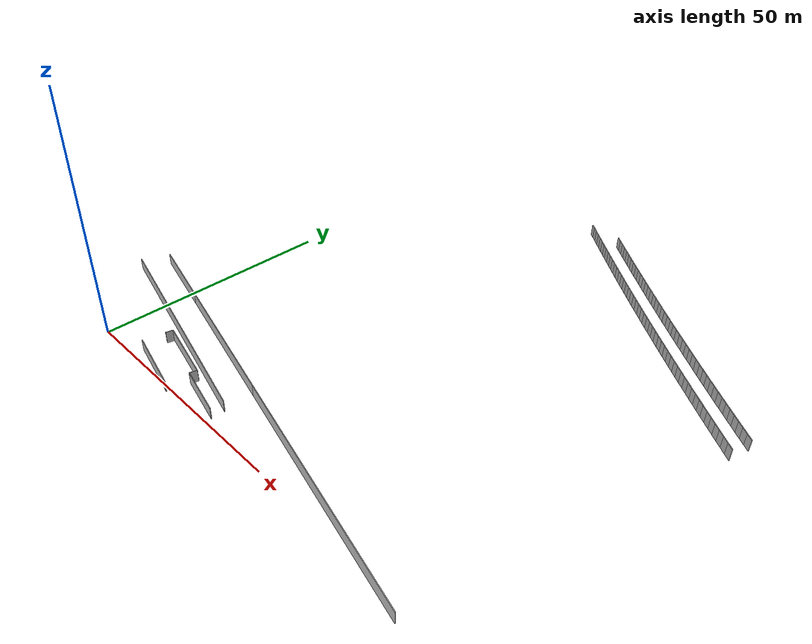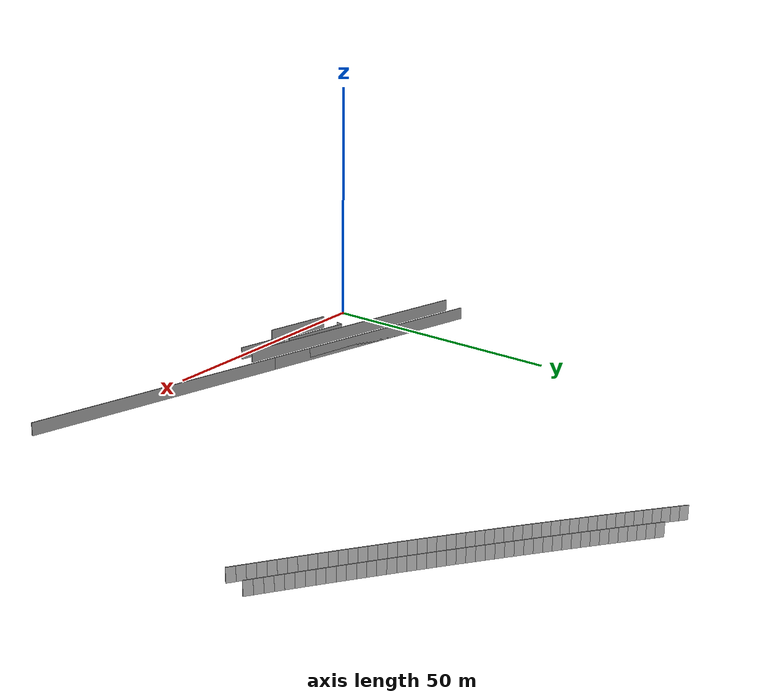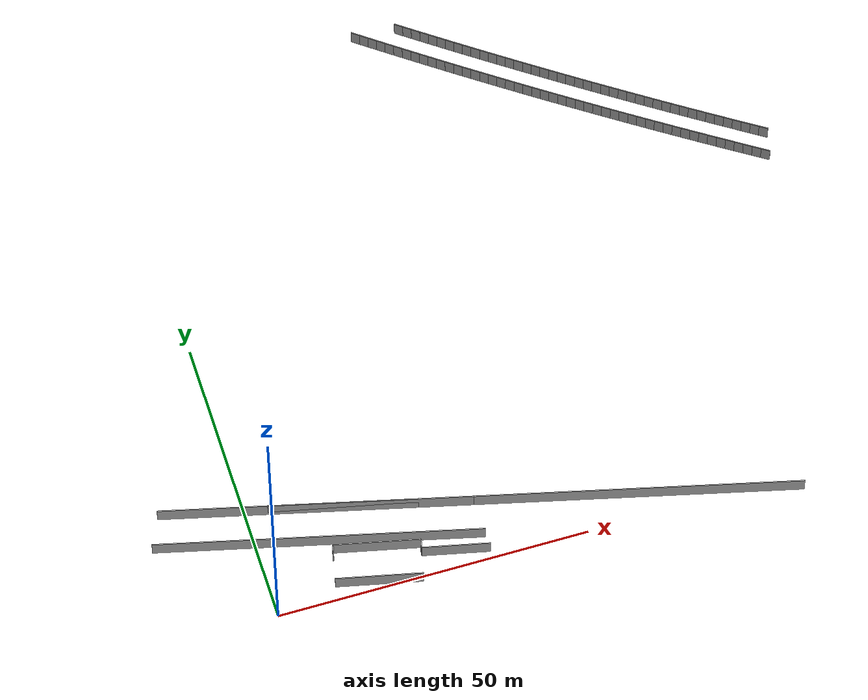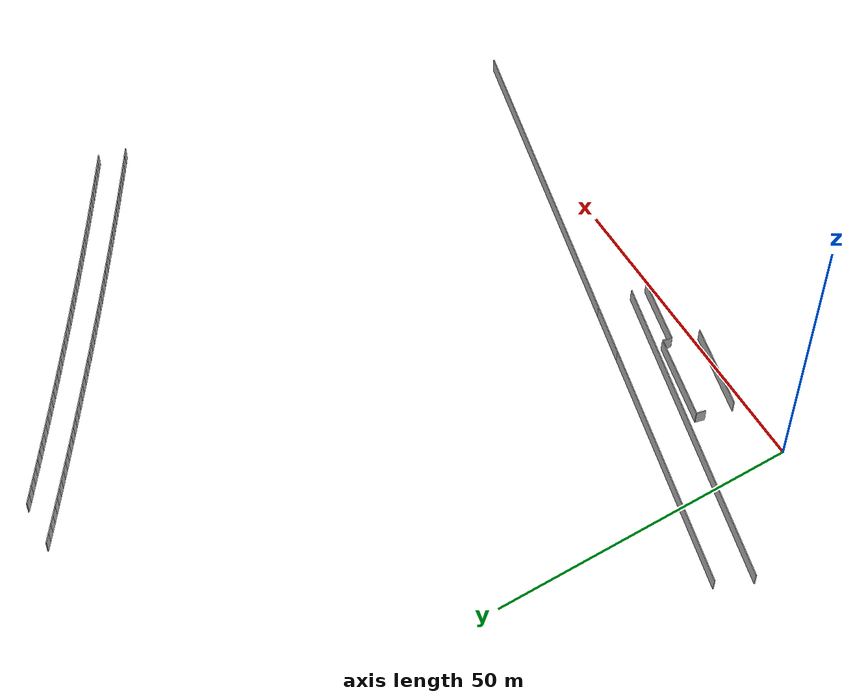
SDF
<?xml version="1.0" ?>
<sdf version="1.6">
  <model name="sps_0503">
    <pose frame="">0 0 0 0 -0 0</pose>
    <static>1</static>
    <self_collide>0</self_collide>
    <allow_auto_disable>0</allow_auto_disable>
    <link name="Wall104">
      <kinematic>0</kinematic>
      <gravity>1</gravity>
      <self_collide>0</self_collide>
      <collision name="collision">
        <geometry>
          <box>
            <size>51.5639 0.15 2.5</size>
          </box>
        </geometry>
        <pose frame="">0 0 0 0 -0 0</pose>
      </collision>
      <visual name="visual">
        <geometry>
          <box>
            <size>51.5639 0.15 2.5</size>
          </box>
        </geometry>
        <pose frame="">0 0 0 0 -0 0</pose>
        <cast_shadows>1</cast_shadows>
        <transparency>0.0</transparency>
      </visual>
      <pose frame="">9.46944 10.2681 1.25 0 0 -0.246916</pose>
    </link>
    <link name="Wall180">
      <kinematic>0</kinematic>
      <gravity>1</gravity>
      <self_collide>0</self_collide>
      <collision name="collision">
        <geometry>
          <box>
            <size>51.5805 0.15 2.5</size>
          </box>
        </geometry>
        <pose frame="">0 0 0 0 -0 0</pose>
      </collision>
      <visual name="visual">
        <geometry>
          <box>
            <size>51.5805 0.15 2.5</size>
          </box>
        </geometry>
        <pose frame="">0 0 0 0 -0 0</pose>
        <cast_shadows>1</cast_shadows>
        <transparency>0.0</transparency>
      </visual>
      <pose frame="">59.4694 3.69687 1.25 0 -0 2.89341</pose>
    </link>
    <link name="Wall181">
      <kinematic>0</kinematic>
      <gravity>1</gravity>
      <self_collide>0</self_collide>
      <collision name="collision">
        <geometry>
          <box>
            <size>32.001 0.15 2.5</size>
          </box>
        </geometry>
        <pose frame="">0 0 0 0 -0 0</pose>
      </collision>
      <visual name="visual">
        <geometry>
          <box>
            <size>32.001 0.15 2.5</size>
          </box>
        </geometry>
        <pose frame="">0 0 0 0 -0 0</pose>
        <cast_shadows>1</cast_shadows>
        <transparency>0.0</transparency>
      </visual>
      <pose frame="">18.9592 13.9626 1.25 0 -0 2.89341</pose>
    </link>
    <link name="Wall275">
      <kinematic>0</kinematic>
      <gravity>1</gravity>
      <self_collide>0</self_collide>
      <collision name="collision">
        <geometry>
          <box>
            <size>1.49953 0.15 2.5</size>
          </box>
        </geometry>
        <pose frame="">0 0 0 0 -0 0</pose>
      </collision>
      <visual name="visual">
        <geometry>
          <box>
            <size>1.49953 0.15 2.5</size>
          </box>
        </geometry>
        <pose frame="">0 0 0 0 -0 0</pose>
        <cast_shadows>1</cast_shadows>
        <transparency>0.0</transparency>
      </visual>
      <pose frame="">24.2309 4.40401 1.25 0 -0 1.34234</pose>
    </link>
    <link name="Wall337">
      <kinematic>0</kinematic>
      <gravity>1</gravity>
      <self_collide>0</self_collide>
      <collision name="collision">
        <geometry>
          <box>
            <size>13.6502 0.15 2.5</size>
          </box>
        </geometry>
        <pose frame="">0 0 0 0 -0 0</pose>
      </collision>
      <visual name="visual">
        <geometry>
          <box>
            <size>13.6502 0.15 2.5</size>
          </box>
        </geometry>
        <pose frame="">0 0 0 0 -0 0</pose>
        <cast_shadows>1</cast_shadows>
        <transparency>0.0</transparency>
      </visual>
      <pose frame="">16.3896 0.810378 1.25 0 -0 2.91335</pose>
    </link>
    <link name="Wall342">
      <kinematic>0</kinematic>
      <gravity>1</gravity>
      <self_collide>0</self_collide>
      <collision name="collision">
        <geometry>
          <box>
            <size>10.6855 0.15 2.5</size>
          </box>
        </geometry>
        <pose frame="">0 0 0 0 -0 0</pose>
      </collision>
      <visual name="visual">
        <geometry>
          <box>
            <size>10.6855 0.15 2.5</size>
          </box>
        </geometry>
        <pose frame="">0 0 0 0 -0 0</pose>
        <cast_shadows>1</cast_shadows>
        <transparency>0.0</transparency>
      </visual>
      <pose frame="">29.2653 2.46477 1.25 0 -0 2.91334</pose>
    </link>
    <link name="Wall421">
      <kinematic>0</kinematic>
      <gravity>1</gravity>
      <self_collide>0</self_collide>
      <collision name="collision">
        <geometry>
          <box>
            <size>13.6503 0.15 2.5</size>
          </box>
        </geometry>
        <pose frame="">0 0 0 0 -0 0</pose>
      </collision>
      <visual name="visual">
        <geometry>
          <box>
            <size>13.6503 0.15 2.5</size>
          </box>
        </geometry>
        <pose frame="">0 0 0 0 -0 0</pose>
        <cast_shadows>1</cast_shadows>
        <transparency>0.0</transparency>
      </visual>
      <pose frame="">17.7526 6.67909 1.25 0 -0 2.91327</pose>
    </link>
    <link name="Wall596">
      <kinematic>0</kinematic>
      <gravity>1</gravity>
      <self_collide>0</self_collide>
      <collision name="collision">
        <geometry>
          <box>
            <size>1.5008 0.15 2.5</size>
          </box>
        </geometry>
        <pose frame="">0 0 0 0 -0 0</pose>
      </collision>
      <visual name="visual">
        <geometry>
          <box>
            <size>1.5008 0.15 2.5</size>
          </box>
        </geometry>
        <pose frame="">0 0 0 0 -0 0</pose>
        <cast_shadows>1</cast_shadows>
        <transparency>0.0</transparency>
      </visual>
      <pose frame="">10.9351 7.4929 1.25 0 0 -1.79876</pose>
    </link>
    <link name="Wall1406">
      <kinematic>0</kinematic>
      <gravity>1</gravity>
      <self_collide>0</self_collide>
      <collision name="collision">
        <geometry>
          <box>
            <size>40.6119 0.15 2.5</size>
          </box>
        </geometry>
        <pose frame="">0 0 0 0 -0 0</pose>
      </collision>
      <visual name="visual">
        <geometry>
          <box>
            <size>40.6119 0.15 2.5</size>
          </box>
        </geometry>
        <pose frame="">0 0 0 0 -0 0</pose>
        <cast_shadows>1</cast_shadows>
        <transparency>0.0</transparency>
      </visual>
      <pose frame="">6.51485 17.1161 1.25 0 0 -0.248183</pose>
    </link>
    <link name="Wall8624">
      <kinematic>0</kinematic>
      <gravity>1</gravity>
      <self_collide>0</self_collide>
      <collision name="collision">
        <geometry>
          <box>
            <size>1.4989 0.15 2.5</size>
          </box>
        </geometry>
        <pose frame="">0 0 0 0 -0 0</pose>
      </collision>
      <visual name="visual">
        <geometry>
          <box>
            <size>1.4989 0.15 2.5</size>
          </box>
        </geometry>
        <pose frame="">0 0 0 0 -0 0</pose>
        <cast_shadows>1</cast_shadows>
        <transparency>0.0</transparency>
      </visual>
      <pose frame="">42.1988 99.8224 1.25 0 0 -0.672229</pose>
    </link>
    <link name="Wall8625">
      <kinematic>0</kinematic>
      <gravity>1</gravity>
      <self_collide>0</self_collide>
      <collision name="collision">
        <geometry>
          <box>
            <size>1.49893 0.15 2.5</size>
          </box>
        </geometry>
        <pose frame="">0 0 0 0 -0 0</pose>
      </collision>
      <visual name="visual">
        <geometry>
          <box>
            <size>1.49893 0.15 2.5</size>
          </box>
        </geometry>
        <pose frame="">0 0 0 0 -0 0</pose>
        <cast_shadows>1</cast_shadows>
        <transparency>0.0</transparency>
      </visual>
      <pose frame="">43.3725 98.89 1.25 0 0 -0.670493</pose>
    </link>
    <link name="Wall8626">
      <kinematic>0</kinematic>
      <gravity>1</gravity>
      <self_collide>0</self_collide>
      <collision name="collision">
        <geometry>
          <box>
            <size>1.49896 0.15 2.5</size>
          </box>
        </geometry>
        <pose frame="">0 0 0 0 -0 0</pose>
      </collision>
      <visual name="visual">
        <geometry>
          <box>
            <size>1.49896 0.15 2.5</size>
          </box>
        </geometry>
        <pose frame="">0 0 0 0 -0 0</pose>
        <cast_shadows>1</cast_shadows>
        <transparency>0.0</transparency>
      </visual>
      <pose frame="">44.5476 97.9594 1.25 0 0 -0.669075</pose>
    </link>
    <link name="Wall8627">
      <kinematic>0</kinematic>
      <gravity>1</gravity>
      <self_collide>0</self_collide>
      <collision name="collision">
        <geometry>
          <box>
            <size>1.49874 0.15 2.5</size>
          </box>
        </geometry>
        <pose frame="">0 0 0 0 -0 0</pose>
      </collision>
      <visual name="visual">
        <geometry>
          <box>
            <size>1.49874 0.15 2.5</size>
          </box>
        </geometry>
        <pose frame="">0 0 0 0 -0 0</pose>
        <cast_shadows>1</cast_shadows>
        <transparency>0.0</transparency>
      </visual>
      <pose frame="">45.7241 97.0307 1.25 0 0 -0.667376</pose>
    </link>
    <link name="Wall8628">
      <kinematic>0</kinematic>
      <gravity>1</gravity>
      <self_collide>0</self_collide>
      <collision name="collision">
        <geometry>
          <box>
            <size>1.49906 0.15 2.5</size>
          </box>
        </geometry>
        <pose frame="">0 0 0 0 -0 0</pose>
      </collision>
      <visual name="visual">
        <geometry>
          <box>
            <size>1.49906 0.15 2.5</size>
          </box>
        </geometry>
        <pose frame="">0 0 0 0 -0 0</pose>
        <cast_shadows>1</cast_shadows>
        <transparency>0.0</transparency>
      </visual>
      <pose frame="">46.9021 96.1039 1.25 0 0 -0.665864</pose>
    </link>
    <link name="Wall8629">
      <kinematic>0</kinematic>
      <gravity>1</gravity>
      <self_collide>0</self_collide>
      <collision name="collision">
        <geometry>
          <box>
            <size>1.49913 0.15 2.5</size>
          </box>
        </geometry>
        <pose frame="">0 0 0 0 -0 0</pose>
      </collision>
      <visual name="visual">
        <geometry>
          <box>
            <size>1.49913 0.15 2.5</size>
          </box>
        </geometry>
        <pose frame="">0 0 0 0 -0 0</pose>
        <cast_shadows>1</cast_shadows>
        <transparency>0.0</transparency>
      </visual>
      <pose frame="">48.0817 95.1788 1.25 0 0 -0.664275</pose>
    </link>
    <link name="Wall8630">
      <kinematic>0</kinematic>
      <gravity>1</gravity>
      <self_collide>0</self_collide>
      <collision name="collision">
        <geometry>
          <box>
            <size>1.4989 0.15 2.5</size>
          </box>
        </geometry>
        <pose frame="">0 0 0 0 -0 0</pose>
      </collision>
      <visual name="visual">
        <geometry>
          <box>
            <size>1.4989 0.15 2.5</size>
          </box>
        </geometry>
        <pose frame="">0 0 0 0 -0 0</pose>
        <cast_shadows>1</cast_shadows>
        <transparency>0.0</transparency>
      </visual>
      <pose frame="">49.2627 94.2556 1.25 0 0 -0.66269</pose>
    </link>
    <link name="Wall8631">
      <kinematic>0</kinematic>
      <gravity>1</gravity>
      <self_collide>0</self_collide>
      <collision name="collision">
        <geometry>
          <box>
            <size>1.49901 0.15 2.5</size>
          </box>
        </geometry>
        <pose frame="">0 0 0 0 -0 0</pose>
      </collision>
      <visual name="visual">
        <geometry>
          <box>
            <size>1.49901 0.15 2.5</size>
          </box>
        </geometry>
        <pose frame="">0 0 0 0 -0 0</pose>
        <cast_shadows>1</cast_shadows>
        <transparency>0.0</transparency>
      </visual>
      <pose frame="">50.4451 93.3343 1.25 0 0 -0.661132</pose>
    </link>
    <link name="Wall8632">
      <kinematic>0</kinematic>
      <gravity>1</gravity>
      <self_collide>0</self_collide>
      <collision name="collision">
        <geometry>
          <box>
            <size>1.49874 0.15 2.5</size>
          </box>
        </geometry>
        <pose frame="">0 0 0 0 -0 0</pose>
      </collision>
      <visual name="visual">
        <geometry>
          <box>
            <size>1.49874 0.15 2.5</size>
          </box>
        </geometry>
        <pose frame="">0 0 0 0 -0 0</pose>
        <cast_shadows>1</cast_shadows>
        <transparency>0.0</transparency>
      </visual>
      <pose frame="">51.6288 92.4149 1.25 0 0 -0.659572</pose>
    </link>
    <link name="Wall8633">
      <kinematic>0</kinematic>
      <gravity>1</gravity>
      <self_collide>0</self_collide>
      <collision name="collision">
        <geometry>
          <box>
            <size>1.49896 0.15 2.5</size>
          </box>
        </geometry>
        <pose frame="">0 0 0 0 -0 0</pose>
      </collision>
      <visual name="visual">
        <geometry>
          <box>
            <size>1.49896 0.15 2.5</size>
          </box>
        </geometry>
        <pose frame="">0 0 0 0 -0 0</pose>
        <cast_shadows>1</cast_shadows>
        <transparency>0.0</transparency>
      </visual>
      <pose frame="">52.814 91.4974 1.25 0 0 -0.657965</pose>
    </link>
    <link name="Wall8634">
      <kinematic>0</kinematic>
      <gravity>1</gravity>
      <self_collide>0</self_collide>
      <collision name="collision">
        <geometry>
          <box>
            <size>1.49905 0.15 2.5</size>
          </box>
        </geometry>
        <pose frame="">0 0 0 0 -0 0</pose>
      </collision>
      <visual name="visual">
        <geometry>
          <box>
            <size>1.49905 0.15 2.5</size>
          </box>
        </geometry>
        <pose frame="">0 0 0 0 -0 0</pose>
        <cast_shadows>1</cast_shadows>
        <transparency>0.0</transparency>
      </visual>
      <pose frame="">54.0008 90.5817 1.25 0 0 -0.656376</pose>
    </link>
    <link name="Wall8635">
      <kinematic>0</kinematic>
      <gravity>1</gravity>
      <self_collide>0</self_collide>
      <collision name="collision">
        <geometry>
          <box>
            <size>1.49898 0.15 2.5</size>
          </box>
        </geometry>
        <pose frame="">0 0 0 0 -0 0</pose>
      </collision>
      <visual name="visual">
        <geometry>
          <box>
            <size>1.49898 0.15 2.5</size>
          </box>
        </geometry>
        <pose frame="">0 0 0 0 -0 0</pose>
        <cast_shadows>1</cast_shadows>
        <transparency>0.0</transparency>
      </visual>
      <pose frame="">55.1891 89.6679 1.25 0 0 -0.654715</pose>
    </link>
    <link name="Wall8636">
      <kinematic>0</kinematic>
      <gravity>1</gravity>
      <self_collide>0</self_collide>
      <collision name="collision">
        <geometry>
          <box>
            <size>1.49902 0.15 2.5</size>
          </box>
        </geometry>
        <pose frame="">0 0 0 0 -0 0</pose>
      </collision>
      <visual name="visual">
        <geometry>
          <box>
            <size>1.49902 0.15 2.5</size>
          </box>
        </geometry>
        <pose frame="">0 0 0 0 -0 0</pose>
        <cast_shadows>1</cast_shadows>
        <transparency>0.0</transparency>
      </visual>
      <pose frame="">56.3789 88.756 1.25 0 0 -0.653208</pose>
    </link>
    <link name="Wall8637">
      <kinematic>0</kinematic>
      <gravity>1</gravity>
      <self_collide>0</self_collide>
      <collision name="collision">
        <geometry>
          <box>
            <size>1.49898 0.15 2.5</size>
          </box>
        </geometry>
        <pose frame="">0 0 0 0 -0 0</pose>
      </collision>
      <visual name="visual">
        <geometry>
          <box>
            <size>1.49898 0.15 2.5</size>
          </box>
        </geometry>
        <pose frame="">0 0 0 0 -0 0</pose>
        <cast_shadows>1</cast_shadows>
        <transparency>0.0</transparency>
      </visual>
      <pose frame="">57.57 87.8459 1.25 0 0 -0.651694</pose>
    </link>
    <link name="Wall8638">
      <kinematic>0</kinematic>
      <gravity>1</gravity>
      <self_collide>0</self_collide>
      <collision name="collision">
        <geometry>
          <box>
            <size>1.49891 0.15 2.5</size>
          </box>
        </geometry>
        <pose frame="">0 0 0 0 -0 0</pose>
      </collision>
      <visual name="visual">
        <geometry>
          <box>
            <size>1.49891 0.15 2.5</size>
          </box>
        </geometry>
        <pose frame="">0 0 0 0 -0 0</pose>
        <cast_shadows>1</cast_shadows>
        <transparency>0.0</transparency>
      </visual>
      <pose frame="">58.7624 86.9377 1.25 0 0 -0.65009</pose>
    </link>
    <link name="Wall8639">
      <kinematic>0</kinematic>
      <gravity>1</gravity>
      <self_collide>0</self_collide>
      <collision name="collision">
        <geometry>
          <box>
            <size>1.49866 0.15 2.5</size>
          </box>
        </geometry>
        <pose frame="">0 0 0 0 -0 0</pose>
      </collision>
      <visual name="visual">
        <geometry>
          <box>
            <size>1.49866 0.15 2.5</size>
          </box>
        </geometry>
        <pose frame="">0 0 0 0 -0 0</pose>
        <cast_shadows>1</cast_shadows>
        <transparency>0.0</transparency>
      </visual>
      <pose frame="">59.9562 86.0315 1.25 0 0 -0.648527</pose>
    </link>
    <link name="Wall8640">
      <kinematic>0</kinematic>
      <gravity>1</gravity>
      <self_collide>0</self_collide>
      <collision name="collision">
        <geometry>
          <box>
            <size>1.49913 0.15 2.5</size>
          </box>
        </geometry>
        <pose frame="">0 0 0 0 -0 0</pose>
      </collision>
      <visual name="visual">
        <geometry>
          <box>
            <size>1.49913 0.15 2.5</size>
          </box>
        </geometry>
        <pose frame="">0 0 0 0 -0 0</pose>
        <cast_shadows>1</cast_shadows>
        <transparency>0.0</transparency>
      </visual>
      <pose frame="">61.1515 85.1271 1.25 0 0 -0.646913</pose>
    </link>
    <link name="Wall8641">
      <kinematic>0</kinematic>
      <gravity>1</gravity>
      <self_collide>0</self_collide>
      <collision name="collision">
        <geometry>
          <box>
            <size>1.49892 0.15 2.5</size>
          </box>
        </geometry>
        <pose frame="">0 0 0 0 -0 0</pose>
      </collision>
      <visual name="visual">
        <geometry>
          <box>
            <size>1.49892 0.15 2.5</size>
          </box>
        </geometry>
        <pose frame="">0 0 0 0 -0 0</pose>
        <cast_shadows>1</cast_shadows>
        <transparency>0.0</transparency>
      </visual>
      <pose frame="">62.3484 84.2246 1.25 0 0 -0.645236</pose>
    </link>
    <link name="Wall8642">
      <kinematic>0</kinematic>
      <gravity>1</gravity>
      <self_collide>0</self_collide>
      <collision name="collision">
        <geometry>
          <box>
            <size>1.4991 0.15 2.5</size>
          </box>
        </geometry>
        <pose frame="">0 0 0 0 -0 0</pose>
      </collision>
      <visual name="visual">
        <geometry>
          <box>
            <size>1.4991 0.15 2.5</size>
          </box>
        </geometry>
        <pose frame="">0 0 0 0 -0 0</pose>
        <cast_shadows>1</cast_shadows>
        <transparency>0.0</transparency>
      </visual>
      <pose frame="">63.5467 83.324 1.25 0 0 -0.64377</pose>
    </link>
    <link name="Wall8643">
      <kinematic>0</kinematic>
      <gravity>1</gravity>
      <self_collide>0</self_collide>
      <collision name="collision">
        <geometry>
          <box>
            <size>1.49871 0.15 2.5</size>
          </box>
        </geometry>
        <pose frame="">0 0 0 0 -0 0</pose>
      </collision>
      <visual name="visual">
        <geometry>
          <box>
            <size>1.49871 0.15 2.5</size>
          </box>
        </geometry>
        <pose frame="">0 0 0 0 -0 0</pose>
        <cast_shadows>1</cast_shadows>
        <transparency>0.0</transparency>
      </visual>
      <pose frame="">64.7464 82.4253 1.25 0 0 -0.642133</pose>
    </link>
    <link name="Wall8644">
      <kinematic>0</kinematic>
      <gravity>1</gravity>
      <self_collide>0</self_collide>
      <collision name="collision">
        <geometry>
          <box>
            <size>1.49892 0.15 2.5</size>
          </box>
        </geometry>
        <pose frame="">0 0 0 0 -0 0</pose>
      </collision>
      <visual name="visual">
        <geometry>
          <box>
            <size>1.49892 0.15 2.5</size>
          </box>
        </geometry>
        <pose frame="">0 0 0 0 -0 0</pose>
        <cast_shadows>1</cast_shadows>
        <transparency>0.0</transparency>
      </visual>
      <pose frame="">65.9473 81.5286 1.25 0 0 -0.640553</pose>
    </link>
    <link name="Wall8645">
      <kinematic>0</kinematic>
      <gravity>1</gravity>
      <self_collide>0</self_collide>
      <collision name="collision">
        <geometry>
          <box>
            <size>1.49895 0.15 2.5</size>
          </box>
        </geometry>
        <pose frame="">0 0 0 0 -0 0</pose>
      </collision>
      <visual name="visual">
        <geometry>
          <box>
            <size>1.49895 0.15 2.5</size>
          </box>
        </geometry>
        <pose frame="">0 0 0 0 -0 0</pose>
        <cast_shadows>1</cast_shadows>
        <transparency>0.0</transparency>
      </visual>
      <pose frame="">67.1498 80.6337 1.25 0 0 -0.639014</pose>
    </link>
    <link name="Wall8646">
      <kinematic>0</kinematic>
      <gravity>1</gravity>
      <self_collide>0</self_collide>
      <collision name="collision">
        <geometry>
          <box>
            <size>1.49897 0.15 2.5</size>
          </box>
        </geometry>
        <pose frame="">0 0 0 0 -0 0</pose>
      </collision>
      <visual name="visual">
        <geometry>
          <box>
            <size>1.49897 0.15 2.5</size>
          </box>
        </geometry>
        <pose frame="">0 0 0 0 -0 0</pose>
        <cast_shadows>1</cast_shadows>
        <transparency>0.0</transparency>
      </visual>
      <pose frame="">68.3538 79.7407 1.25 0 0 -0.637385</pose>
    </link>
    <link name="Wall8647">
      <kinematic>0</kinematic>
      <gravity>1</gravity>
      <self_collide>0</self_collide>
      <collision name="collision">
        <geometry>
          <box>
            <size>1.49896 0.15 2.5</size>
          </box>
        </geometry>
        <pose frame="">0 0 0 0 -0 0</pose>
      </collision>
      <visual name="visual">
        <geometry>
          <box>
            <size>1.49896 0.15 2.5</size>
          </box>
        </geometry>
        <pose frame="">0 0 0 0 -0 0</pose>
        <cast_shadows>1</cast_shadows>
        <transparency>0.0</transparency>
      </visual>
      <pose frame="">69.5591 78.8496 1.25 0 0 -0.63587</pose>
    </link>
    <link name="Wall8648">
      <kinematic>0</kinematic>
      <gravity>1</gravity>
      <self_collide>0</self_collide>
      <collision name="collision">
        <geometry>
          <box>
            <size>1.49889 0.15 2.5</size>
          </box>
        </geometry>
        <pose frame="">0 0 0 0 -0 0</pose>
      </collision>
      <visual name="visual">
        <geometry>
          <box>
            <size>1.49889 0.15 2.5</size>
          </box>
        </geometry>
        <pose frame="">0 0 0 0 -0 0</pose>
        <cast_shadows>1</cast_shadows>
        <transparency>0.0</transparency>
      </visual>
      <pose frame="">70.7658 77.9604 1.25 0 0 -0.634233</pose>
    </link>
    <link name="Wall8649">
      <kinematic>0</kinematic>
      <gravity>1</gravity>
      <self_collide>0</self_collide>
      <collision name="collision">
        <geometry>
          <box>
            <size>1.49912 0.15 2.5</size>
          </box>
        </geometry>
        <pose frame="">0 0 0 0 -0 0</pose>
      </collision>
      <visual name="visual">
        <geometry>
          <box>
            <size>1.49912 0.15 2.5</size>
          </box>
        </geometry>
        <pose frame="">0 0 0 0 -0 0</pose>
        <cast_shadows>1</cast_shadows>
        <transparency>0.0</transparency>
      </visual>
      <pose frame="">71.974 77.0731 1.25 0 0 -0.632655</pose>
    </link>
    <link name="Wall8650">
      <kinematic>0</kinematic>
      <gravity>1</gravity>
      <self_collide>0</self_collide>
      <collision name="collision">
        <geometry>
          <box>
            <size>1.49892 0.15 2.5</size>
          </box>
        </geometry>
        <pose frame="">0 0 0 0 -0 0</pose>
      </collision>
      <visual name="visual">
        <geometry>
          <box>
            <size>1.49892 0.15 2.5</size>
          </box>
        </geometry>
        <pose frame="">0 0 0 0 -0 0</pose>
        <cast_shadows>1</cast_shadows>
        <transparency>0.0</transparency>
      </visual>
      <pose frame="">73.1836 76.1877 1.25 0 0 -0.63109</pose>
    </link>
    <link name="Wall8651">
      <kinematic>0</kinematic>
      <gravity>1</gravity>
      <self_collide>0</self_collide>
      <collision name="collision">
        <geometry>
          <box>
            <size>1.49901 0.15 2.5</size>
          </box>
        </geometry>
        <pose frame="">0 0 0 0 -0 0</pose>
      </collision>
      <visual name="visual">
        <geometry>
          <box>
            <size>1.49901 0.15 2.5</size>
          </box>
        </geometry>
        <pose frame="">0 0 0 0 -0 0</pose>
        <cast_shadows>1</cast_shadows>
        <transparency>0.0</transparency>
      </visual>
      <pose frame="">74.3945 75.3042 1.25 0 0 -0.629584</pose>
    </link>
    <link name="Wall8652">
      <kinematic>0</kinematic>
      <gravity>1</gravity>
      <self_collide>0</self_collide>
      <collision name="collision">
        <geometry>
          <box>
            <size>1.49882 0.15 2.5</size>
          </box>
        </geometry>
        <pose frame="">0 0 0 0 -0 0</pose>
      </collision>
      <visual name="visual">
        <geometry>
          <box>
            <size>1.49882 0.15 2.5</size>
          </box>
        </geometry>
        <pose frame="">0 0 0 0 -0 0</pose>
        <cast_shadows>1</cast_shadows>
        <transparency>0.0</transparency>
      </visual>
      <pose frame="">75.6068 74.4227 1.25 0 0 -0.627814</pose>
    </link>
    <link name="Wall8653">
      <kinematic>0</kinematic>
      <gravity>1</gravity>
      <self_collide>0</self_collide>
      <collision name="collision">
        <geometry>
          <box>
            <size>1.49897 0.15 2.5</size>
          </box>
        </geometry>
        <pose frame="">0 0 0 0 -0 0</pose>
      </collision>
      <visual name="visual">
        <geometry>
          <box>
            <size>1.49897 0.15 2.5</size>
          </box>
        </geometry>
        <pose frame="">0 0 0 0 -0 0</pose>
        <cast_shadows>1</cast_shadows>
        <transparency>0.0</transparency>
      </visual>
      <pose frame="">76.8205 73.5431 1.25 0 0 -0.626431</pose>
    </link>
    <link name="Wall8654">
      <kinematic>0</kinematic>
      <gravity>1</gravity>
      <self_collide>0</self_collide>
      <collision name="collision">
        <geometry>
          <box>
            <size>1.49891 0.15 2.5</size>
          </box>
        </geometry>
        <pose frame="">0 0 0 0 -0 0</pose>
      </collision>
      <visual name="visual">
        <geometry>
          <box>
            <size>1.49891 0.15 2.5</size>
          </box>
        </geometry>
        <pose frame="">0 0 0 0 -0 0</pose>
        <cast_shadows>1</cast_shadows>
        <transparency>0.0</transparency>
      </visual>
      <pose frame="">78.0355 72.6654 1.25 0 0 -0.624704</pose>
    </link>
    <link name="Wall8655">
      <kinematic>0</kinematic>
      <gravity>1</gravity>
      <self_collide>0</self_collide>
      <collision name="collision">
        <geometry>
          <box>
            <size>1.49889 0.15 2.5</size>
          </box>
        </geometry>
        <pose frame="">0 0 0 0 -0 0</pose>
      </collision>
      <visual name="visual">
        <geometry>
          <box>
            <size>1.49889 0.15 2.5</size>
          </box>
        </geometry>
        <pose frame="">0 0 0 0 -0 0</pose>
        <cast_shadows>1</cast_shadows>
        <transparency>0.0</transparency>
      </visual>
      <pose frame="">79.2519 71.7896 1.25 0 0 -0.623359</pose>
    </link>
    <link name="Wall8656">
      <kinematic>0</kinematic>
      <gravity>1</gravity>
      <self_collide>0</self_collide>
      <collision name="collision">
        <geometry>
          <box>
            <size>1.49905 0.15 2.5</size>
          </box>
        </geometry>
        <pose frame="">0 0 0 0 -0 0</pose>
      </collision>
      <visual name="visual">
        <geometry>
          <box>
            <size>1.49905 0.15 2.5</size>
          </box>
        </geometry>
        <pose frame="">0 0 0 0 -0 0</pose>
        <cast_shadows>1</cast_shadows>
        <transparency>0.0</transparency>
      </visual>
      <pose frame="">80.4697 70.9156 1.25 0 0 -0.621627</pose>
    </link>
    <link name="Wall8657">
      <kinematic>0</kinematic>
      <gravity>1</gravity>
      <self_collide>0</self_collide>
      <collision name="collision">
        <geometry>
          <box>
            <size>1.49897 0.15 2.5</size>
          </box>
        </geometry>
        <pose frame="">0 0 0 0 -0 0</pose>
      </collision>
      <visual name="visual">
        <geometry>
          <box>
            <size>1.49897 0.15 2.5</size>
          </box>
        </geometry>
        <pose frame="">0 0 0 0 -0 0</pose>
        <cast_shadows>1</cast_shadows>
        <transparency>0.0</transparency>
      </visual>
      <pose frame="">81.689 70.0436 1.25 0 0 -0.620013</pose>
    </link>
    <link name="Wall8658">
      <kinematic>0</kinematic>
      <gravity>1</gravity>
      <self_collide>0</self_collide>
      <collision name="collision">
        <geometry>
          <box>
            <size>1.49888 0.15 2.5</size>
          </box>
        </geometry>
        <pose frame="">0 0 0 0 -0 0</pose>
      </collision>
      <visual name="visual">
        <geometry>
          <box>
            <size>1.49888 0.15 2.5</size>
          </box>
        </geometry>
        <pose frame="">0 0 0 0 -0 0</pose>
        <cast_shadows>1</cast_shadows>
        <transparency>0.0</transparency>
      </visual>
      <pose frame="">82.9097 69.1736 1.25 0 0 -0.618455</pose>
    </link>
    <link name="Wall8659">
      <kinematic>0</kinematic>
      <gravity>1</gravity>
      <self_collide>0</self_collide>
      <collision name="collision">
        <geometry>
          <box>
            <size>1.49896 0.15 2.5</size>
          </box>
        </geometry>
        <pose frame="">0 0 0 0 -0 0</pose>
      </collision>
      <visual name="visual">
        <geometry>
          <box>
            <size>1.49896 0.15 2.5</size>
          </box>
        </geometry>
        <pose frame="">0 0 0 0 -0 0</pose>
        <cast_shadows>1</cast_shadows>
        <transparency>0.0</transparency>
      </visual>
      <pose frame="">84.1317 68.3056 1.25 0 0 -0.61677</pose>
    </link>
    <link name="Wall8660">
      <kinematic>0</kinematic>
      <gravity>1</gravity>
      <self_collide>0</self_collide>
      <collision name="collision">
        <geometry>
          <box>
            <size>1.49905 0.15 2.5</size>
          </box>
        </geometry>
        <pose frame="">0 0 0 0 -0 0</pose>
      </collision>
      <visual name="visual">
        <geometry>
          <box>
            <size>1.49905 0.15 2.5</size>
          </box>
        </geometry>
        <pose frame="">0 0 0 0 -0 0</pose>
        <cast_shadows>1</cast_shadows>
        <transparency>0.0</transparency>
      </visual>
      <pose frame="">85.3552 67.4395 1.25 0 0 -0.615232</pose>
    </link>
    <link name="Wall8661">
      <kinematic>0</kinematic>
      <gravity>1</gravity>
      <self_collide>0</self_collide>
      <collision name="collision">
        <geometry>
          <box>
            <size>1.49877 0.15 2.5</size>
          </box>
        </geometry>
        <pose frame="">0 0 0 0 -0 0</pose>
      </collision>
      <visual name="visual">
        <geometry>
          <box>
            <size>1.49877 0.15 2.5</size>
          </box>
        </geometry>
        <pose frame="">0 0 0 0 -0 0</pose>
        <cast_shadows>1</cast_shadows>
        <transparency>0.0</transparency>
      </visual>
      <pose frame="">86.5799 66.5753 1.25 0 0 -0.613769</pose>
    </link>
    <link name="Wall8662">
      <kinematic>0</kinematic>
      <gravity>1</gravity>
      <self_collide>0</self_collide>
      <collision name="collision">
        <geometry>
          <box>
            <size>1.49901 0.15 2.5</size>
          </box>
        </geometry>
        <pose frame="">0 0 0 0 -0 0</pose>
      </collision>
      <visual name="visual">
        <geometry>
          <box>
            <size>1.49901 0.15 2.5</size>
          </box>
        </geometry>
        <pose frame="">0 0 0 0 -0 0</pose>
        <cast_shadows>1</cast_shadows>
        <transparency>0.0</transparency>
      </visual>
      <pose frame="">87.8059 65.713 1.25 0 0 -0.61216</pose>
    </link>
    <link name="Wall8663">
      <kinematic>0</kinematic>
      <gravity>1</gravity>
      <self_collide>0</self_collide>
      <collision name="collision">
        <geometry>
          <box>
            <size>1.4987 0.15 2.5</size>
          </box>
        </geometry>
        <pose frame="">0 0 0 0 -0 0</pose>
      </collision>
      <visual name="visual">
        <geometry>
          <box>
            <size>1.4987 0.15 2.5</size>
          </box>
        </geometry>
        <pose frame="">0 0 0 0 -0 0</pose>
        <cast_shadows>1</cast_shadows>
        <transparency>0.0</transparency>
      </visual>
      <pose frame="">89.0333 64.8527 1.25 0 0 -0.610516</pose>
    </link>
    <link name="Wall8664">
      <kinematic>0</kinematic>
      <gravity>1</gravity>
      <self_collide>0</self_collide>
      <collision name="collision">
        <geometry>
          <box>
            <size>1.49915 0.15 2.5</size>
          </box>
        </geometry>
        <pose frame="">0 0 0 0 -0 0</pose>
      </collision>
      <visual name="visual">
        <geometry>
          <box>
            <size>1.49915 0.15 2.5</size>
          </box>
        </geometry>
        <pose frame="">0 0 0 0 -0 0</pose>
        <cast_shadows>1</cast_shadows>
        <transparency>0.0</transparency>
      </visual>
      <pose frame="">90.262 63.9943 1.25 0 0 -0.609018</pose>
    </link>
    <link name="Wall8665">
      <kinematic>0</kinematic>
      <gravity>1</gravity>
      <self_collide>0</self_collide>
      <collision name="collision">
        <geometry>
          <box>
            <size>1.49884 0.15 2.5</size>
          </box>
        </geometry>
        <pose frame="">0 0 0 0 -0 0</pose>
      </collision>
      <visual name="visual">
        <geometry>
          <box>
            <size>1.49884 0.15 2.5</size>
          </box>
        </geometry>
        <pose frame="">0 0 0 0 -0 0</pose>
        <cast_shadows>1</cast_shadows>
        <transparency>0.0</transparency>
      </visual>
      <pose frame="">91.4922 63.1378 1.25 0 0 -0.607373</pose>
    </link>
    <link name="Wall8666">
      <kinematic>0</kinematic>
      <gravity>1</gravity>
      <self_collide>0</self_collide>
      <collision name="collision">
        <geometry>
          <box>
            <size>1.49914 0.15 2.5</size>
          </box>
        </geometry>
        <pose frame="">0 0 0 0 -0 0</pose>
      </collision>
      <visual name="visual">
        <geometry>
          <box>
            <size>1.49914 0.15 2.5</size>
          </box>
        </geometry>
        <pose frame="">0 0 0 0 -0 0</pose>
        <cast_shadows>1</cast_shadows>
        <transparency>0.0</transparency>
      </visual>
      <pose frame="">92.7237 62.2832 1.25 0 0 -0.605946</pose>
    </link>
    <link name="Wall8667">
      <kinematic>0</kinematic>
      <gravity>1</gravity>
      <self_collide>0</self_collide>
      <collision name="collision">
        <geometry>
          <box>
            <size>1.49871 0.15 2.5</size>
          </box>
        </geometry>
        <pose frame="">0 0 0 0 -0 0</pose>
      </collision>
      <visual name="visual">
        <geometry>
          <box>
            <size>1.49871 0.15 2.5</size>
          </box>
        </geometry>
        <pose frame="">0 0 0 0 -0 0</pose>
        <cast_shadows>1</cast_shadows>
        <transparency>0.0</transparency>
      </visual>
      <pose frame="">93.9566 61.4306 1.25 0 0 -0.604167</pose>
    </link>
    <link name="Wall8668">
      <kinematic>0</kinematic>
      <gravity>1</gravity>
      <self_collide>0</self_collide>
      <collision name="collision">
        <geometry>
          <box>
            <size>1.49901 0.15 2.5</size>
          </box>
        </geometry>
        <pose frame="">0 0 0 0 -0 0</pose>
      </collision>
      <visual name="visual">
        <geometry>
          <box>
            <size>1.49901 0.15 2.5</size>
          </box>
        </geometry>
        <pose frame="">0 0 0 0 -0 0</pose>
        <cast_shadows>1</cast_shadows>
        <transparency>0.0</transparency>
      </visual>
      <pose frame="">95.1908 60.5801 1.25 0 0 -0.602594</pose>
    </link>
    <link name="Wall8669">
      <kinematic>0</kinematic>
      <gravity>1</gravity>
      <self_collide>0</self_collide>
      <collision name="collision">
        <geometry>
          <box>
            <size>1.49898 0.15 2.5</size>
          </box>
        </geometry>
        <pose frame="">0 0 0 0 -0 0</pose>
      </collision>
      <visual name="visual">
        <geometry>
          <box>
            <size>1.49898 0.15 2.5</size>
          </box>
        </geometry>
        <pose frame="">0 0 0 0 -0 0</pose>
        <cast_shadows>1</cast_shadows>
        <transparency>0.0</transparency>
      </visual>
      <pose frame="">96.4264 59.7314 1.25 0 0 -0.601126</pose>
    </link>
    <link name="Wall8670">
      <kinematic>0</kinematic>
      <gravity>1</gravity>
      <self_collide>0</self_collide>
      <collision name="collision">
        <geometry>
          <box>
            <size>1.49888 0.15 2.5</size>
          </box>
        </geometry>
        <pose frame="">0 0 0 0 -0 0</pose>
      </collision>
      <visual name="visual">
        <geometry>
          <box>
            <size>1.49888 0.15 2.5</size>
          </box>
        </geometry>
        <pose frame="">0 0 0 0 -0 0</pose>
        <cast_shadows>1</cast_shadows>
        <transparency>0.0</transparency>
      </visual>
      <pose frame="">97.6632 58.8846 1.25 0 0 -0.59959</pose>
    </link>
    <link name="Wall8671">
      <kinematic>0</kinematic>
      <gravity>1</gravity>
      <self_collide>0</self_collide>
      <collision name="collision">
        <geometry>
          <box>
            <size>1.49901 0.15 2.5</size>
          </box>
        </geometry>
        <pose frame="">0 0 0 0 -0 0</pose>
      </collision>
      <visual name="visual">
        <geometry>
          <box>
            <size>1.49901 0.15 2.5</size>
          </box>
        </geometry>
        <pose frame="">0 0 0 0 -0 0</pose>
        <cast_shadows>1</cast_shadows>
        <transparency>0.0</transparency>
      </visual>
      <pose frame="">98.9014 58.0398 1.25 0 0 -0.597907</pose>
    </link>
    <link name="Wall9709">
      <kinematic>0</kinematic>
      <gravity>1</gravity>
      <self_collide>0</self_collide>
      <collision name="collision">
        <geometry>
          <box>
            <size>1.49233 0.15 2.5</size>
          </box>
        </geometry>
        <pose frame="">0 0 0 0 -0 0</pose>
      </collision>
      <visual name="visual">
        <geometry>
          <box>
            <size>1.49233 0.15 2.5</size>
          </box>
        </geometry>
        <pose frame="">0 0 0 0 -0 0</pose>
        <cast_shadows>1</cast_shadows>
        <transparency>0.0</transparency>
      </visual>
      <pose frame="">49.4594 99.3598 1.25 0 0 -0.665818</pose>
    </link>
    <link name="Wall9710">
      <kinematic>0</kinematic>
      <gravity>1</gravity>
      <self_collide>0</self_collide>
      <collision name="collision">
        <geometry>
          <box>
            <size>1.49261 0.15 2.5</size>
          </box>
        </geometry>
        <pose frame="">0 0 0 0 -0 0</pose>
      </collision>
      <visual name="visual">
        <geometry>
          <box>
            <size>1.49261 0.15 2.5</size>
          </box>
        </geometry>
        <pose frame="">0 0 0 0 -0 0</pose>
        <cast_shadows>1</cast_shadows>
        <transparency>0.0</transparency>
      </visual>
      <pose frame="">50.6338 98.4388 1.25 0 0 -0.664267</pose>
    </link>
    <link name="Wall9711">
      <kinematic>0</kinematic>
      <gravity>1</gravity>
      <self_collide>0</self_collide>
      <collision name="collision">
        <geometry>
          <box>
            <size>1.49232 0.15 2.5</size>
          </box>
        </geometry>
        <pose frame="">0 0 0 0 -0 0</pose>
      </collision>
      <visual name="visual">
        <geometry>
          <box>
            <size>1.49232 0.15 2.5</size>
          </box>
        </geometry>
        <pose frame="">0 0 0 0 -0 0</pose>
        <cast_shadows>1</cast_shadows>
        <transparency>0.0</transparency>
      </visual>
      <pose frame="">51.8097 97.5196 1.25 0 0 -0.662758</pose>
    </link>
    <link name="Wall9712">
      <kinematic>0</kinematic>
      <gravity>1</gravity>
      <self_collide>0</self_collide>
      <collision name="collision">
        <geometry>
          <box>
            <size>1.49244 0.15 2.5</size>
          </box>
        </geometry>
        <pose frame="">0 0 0 0 -0 0</pose>
      </collision>
      <visual name="visual">
        <geometry>
          <box>
            <size>1.49244 0.15 2.5</size>
          </box>
        </geometry>
        <pose frame="">0 0 0 0 -0 0</pose>
        <cast_shadows>1</cast_shadows>
        <transparency>0.0</transparency>
      </visual>
      <pose frame="">52.9868 96.6023 1.25 0 0 -0.661136</pose>
    </link>
    <link name="Wall9713">
      <kinematic>0</kinematic>
      <gravity>1</gravity>
      <self_collide>0</self_collide>
      <collision name="collision">
        <geometry>
          <box>
            <size>1.4924 0.15 2.5</size>
          </box>
        </geometry>
        <pose frame="">0 0 0 0 -0 0</pose>
      </collision>
      <visual name="visual">
        <geometry>
          <box>
            <size>1.4924 0.15 2.5</size>
          </box>
        </geometry>
        <pose frame="">0 0 0 0 -0 0</pose>
        <cast_shadows>1</cast_shadows>
        <transparency>0.0</transparency>
      </visual>
      <pose frame="">54.1655 95.6869 1.25 0 0 -0.659501</pose>
    </link>
    <link name="Wall9714">
      <kinematic>0</kinematic>
      <gravity>1</gravity>
      <self_collide>0</self_collide>
      <collision name="collision">
        <geometry>
          <box>
            <size>1.49223 0.15 2.5</size>
          </box>
        </geometry>
        <pose frame="">0 0 0 0 -0 0</pose>
      </collision>
      <visual name="visual">
        <geometry>
          <box>
            <size>1.49223 0.15 2.5</size>
          </box>
        </geometry>
        <pose frame="">0 0 0 0 -0 0</pose>
        <cast_shadows>1</cast_shadows>
        <transparency>0.0</transparency>
      </visual>
      <pose frame="">55.3457 94.7735 1.25 0 0 -0.657883</pose>
    </link>
    <link name="Wall9715">
      <kinematic>0</kinematic>
      <gravity>1</gravity>
      <self_collide>0</self_collide>
      <collision name="collision">
        <geometry>
          <box>
            <size>1.49248 0.15 2.5</size>
          </box>
        </geometry>
        <pose frame="">0 0 0 0 -0 0</pose>
      </collision>
      <visual name="visual">
        <geometry>
          <box>
            <size>1.49248 0.15 2.5</size>
          </box>
        </geometry>
        <pose frame="">0 0 0 0 -0 0</pose>
        <cast_shadows>1</cast_shadows>
        <transparency>0.0</transparency>
      </visual>
      <pose frame="">56.5272 93.8619 1.25 0 0 -0.656359</pose>
    </link>
    <link name="Wall9716">
      <kinematic>0</kinematic>
      <gravity>1</gravity>
      <self_collide>0</self_collide>
      <collision name="collision">
        <geometry>
          <box>
            <size>1.49242 0.15 2.5</size>
          </box>
        </geometry>
        <pose frame="">0 0 0 0 -0 0</pose>
      </collision>
      <visual name="visual">
        <geometry>
          <box>
            <size>1.49242 0.15 2.5</size>
          </box>
        </geometry>
        <pose frame="">0 0 0 0 -0 0</pose>
        <cast_shadows>1</cast_shadows>
        <transparency>0.0</transparency>
      </visual>
      <pose frame="">57.7103 92.952 1.25 0 0 -0.654895</pose>
    </link>
    <link name="Wall9717">
      <kinematic>0</kinematic>
      <gravity>1</gravity>
      <self_collide>0</self_collide>
      <collision name="collision">
        <geometry>
          <box>
            <size>1.49244 0.15 2.5</size>
          </box>
        </geometry>
        <pose frame="">0 0 0 0 -0 0</pose>
      </collision>
      <visual name="visual">
        <geometry>
          <box>
            <size>1.49244 0.15 2.5</size>
          </box>
        </geometry>
        <pose frame="">0 0 0 0 -0 0</pose>
        <cast_shadows>1</cast_shadows>
        <transparency>0.0</transparency>
      </visual>
      <pose frame="">58.8947 92.044 1.25 0 0 -0.653235</pose>
    </link>
    <link name="Wall9718">
      <kinematic>0</kinematic>
      <gravity>1</gravity>
      <self_collide>0</self_collide>
      <collision name="collision">
        <geometry>
          <box>
            <size>1.49241 0.15 2.5</size>
          </box>
        </geometry>
        <pose frame="">0 0 0 0 -0 0</pose>
      </collision>
      <visual name="visual">
        <geometry>
          <box>
            <size>1.49241 0.15 2.5</size>
          </box>
        </geometry>
        <pose frame="">0 0 0 0 -0 0</pose>
        <cast_shadows>1</cast_shadows>
        <transparency>0.0</transparency>
      </visual>
      <pose frame="">60.0806 91.1379 1.25 0 0 -0.651656</pose>
    </link>
    <link name="Wall9719">
      <kinematic>0</kinematic>
      <gravity>1</gravity>
      <self_collide>0</self_collide>
      <collision name="collision">
        <geometry>
          <box>
            <size>1.49234 0.15 2.5</size>
          </box>
        </geometry>
        <pose frame="">0 0 0 0 -0 0</pose>
      </collision>
      <visual name="visual">
        <geometry>
          <box>
            <size>1.49234 0.15 2.5</size>
          </box>
        </geometry>
        <pose frame="">0 0 0 0 -0 0</pose>
        <cast_shadows>1</cast_shadows>
        <transparency>0.0</transparency>
      </visual>
      <pose frame="">61.2678 90.2337 1.25 0 0 -0.650045</pose>
    </link>
    <link name="Wall9720">
      <kinematic>0</kinematic>
      <gravity>1</gravity>
      <self_collide>0</self_collide>
      <collision name="collision">
        <geometry>
          <box>
            <size>1.49239 0.15 2.5</size>
          </box>
        </geometry>
        <pose frame="">0 0 0 0 -0 0</pose>
      </collision>
      <visual name="visual">
        <geometry>
          <box>
            <size>1.49239 0.15 2.5</size>
          </box>
        </geometry>
        <pose frame="">0 0 0 0 -0 0</pose>
        <cast_shadows>1</cast_shadows>
        <transparency>0.0</transparency>
      </visual>
      <pose frame="">62.4565 89.3314 1.25 0 0 -0.648532</pose>
    </link>
    <link name="Wall9721">
      <kinematic>0</kinematic>
      <gravity>1</gravity>
      <self_collide>0</self_collide>
      <collision name="collision">
        <geometry>
          <box>
            <size>1.49249 0.15 2.5</size>
          </box>
        </geometry>
        <pose frame="">0 0 0 0 -0 0</pose>
      </collision>
      <visual name="visual">
        <geometry>
          <box>
            <size>1.49249 0.15 2.5</size>
          </box>
        </geometry>
        <pose frame="">0 0 0 0 -0 0</pose>
        <cast_shadows>1</cast_shadows>
        <transparency>0.0</transparency>
      </visual>
      <pose frame="">63.6468 88.431 1.25 0 0 -0.646789</pose>
    </link>
    <link name="Wall9722">
      <kinematic>0</kinematic>
      <gravity>1</gravity>
      <self_collide>0</self_collide>
      <collision name="collision">
        <geometry>
          <box>
            <size>1.49246 0.15 2.5</size>
          </box>
        </geometry>
        <pose frame="">0 0 0 0 -0 0</pose>
      </collision>
      <visual name="visual">
        <geometry>
          <box>
            <size>1.49246 0.15 2.5</size>
          </box>
        </geometry>
        <pose frame="">0 0 0 0 -0 0</pose>
        <cast_shadows>1</cast_shadows>
        <transparency>0.0</transparency>
      </visual>
      <pose frame="">64.8385 87.5325 1.25 0 0 -0.645268</pose>
    </link>
    <link name="Wall9723">
      <kinematic>0</kinematic>
      <gravity>1</gravity>
      <self_collide>0</self_collide>
      <collision name="collision">
        <geometry>
          <box>
            <size>1.49252 0.15 2.5</size>
          </box>
        </geometry>
        <pose frame="">0 0 0 0 -0 0</pose>
      </collision>
      <visual name="visual">
        <geometry>
          <box>
            <size>1.49252 0.15 2.5</size>
          </box>
        </geometry>
        <pose frame="">0 0 0 0 -0 0</pose>
        <cast_shadows>1</cast_shadows>
        <transparency>0.0</transparency>
      </visual>
      <pose frame="">66.0315 86.6358 1.25 0 0 -0.643755</pose>
    </link>
    <link name="Wall9724">
      <kinematic>0</kinematic>
      <gravity>1</gravity>
      <self_collide>0</self_collide>
      <collision name="collision">
        <geometry>
          <box>
            <size>1.49229 0.15 2.5</size>
          </box>
        </geometry>
        <pose frame="">0 0 0 0 -0 0</pose>
      </collision>
      <visual name="visual">
        <geometry>
          <box>
            <size>1.49229 0.15 2.5</size>
          </box>
        </geometry>
        <pose frame="">0 0 0 0 -0 0</pose>
        <cast_shadows>1</cast_shadows>
        <transparency>0.0</transparency>
      </visual>
      <pose frame="">67.2259 85.741 1.25 0 0 -0.642184</pose>
    </link>
    <link name="Wall9725">
      <kinematic>0</kinematic>
      <gravity>1</gravity>
      <self_collide>0</self_collide>
      <collision name="collision">
        <geometry>
          <box>
            <size>1.49246 0.15 2.5</size>
          </box>
        </geometry>
        <pose frame="">0 0 0 0 -0 0</pose>
      </collision>
      <visual name="visual">
        <geometry>
          <box>
            <size>1.49246 0.15 2.5</size>
          </box>
        </geometry>
        <pose frame="">0 0 0 0 -0 0</pose>
        <cast_shadows>1</cast_shadows>
        <transparency>0.0</transparency>
      </visual>
      <pose frame="">68.4217 84.8481 1.25 0 0 -0.640565</pose>
    </link>
    <link name="Wall9726">
      <kinematic>0</kinematic>
      <gravity>1</gravity>
      <self_collide>0</self_collide>
      <collision name="collision">
        <geometry>
          <box>
            <size>1.49228 0.15 2.5</size>
          </box>
        </geometry>
        <pose frame="">0 0 0 0 -0 0</pose>
      </collision>
      <visual name="visual">
        <geometry>
          <box>
            <size>1.49228 0.15 2.5</size>
          </box>
        </geometry>
        <pose frame="">0 0 0 0 -0 0</pose>
        <cast_shadows>1</cast_shadows>
        <transparency>0.0</transparency>
      </visual>
      <pose frame="">69.6189 83.9571 1.25 0 0 -0.639027</pose>
    </link>
    <link name="Wall9727">
      <kinematic>0</kinematic>
      <gravity>1</gravity>
      <self_collide>0</self_collide>
      <collision name="collision">
        <geometry>
          <box>
            <size>1.49246 0.15 2.5</size>
          </box>
        </geometry>
        <pose frame="">0 0 0 0 -0 0</pose>
      </collision>
      <visual name="visual">
        <geometry>
          <box>
            <size>1.49246 0.15 2.5</size>
          </box>
        </geometry>
        <pose frame="">0 0 0 0 -0 0</pose>
        <cast_shadows>1</cast_shadows>
        <transparency>0.0</transparency>
      </visual>
      <pose frame="">70.8176 83.068 1.25 0 0 -0.637408</pose>
    </link>
    <link name="Wall9728">
      <kinematic>0</kinematic>
      <gravity>1</gravity>
      <self_collide>0</self_collide>
      <collision name="collision">
        <geometry>
          <box>
            <size>1.49239 0.15 2.5</size>
          </box>
        </geometry>
        <pose frame="">0 0 0 0 -0 0</pose>
      </collision>
      <visual name="visual">
        <geometry>
          <box>
            <size>1.49239 0.15 2.5</size>
          </box>
        </geometry>
        <pose frame="">0 0 0 0 -0 0</pose>
        <cast_shadows>1</cast_shadows>
        <transparency>0.0</transparency>
      </visual>
      <pose frame="">72.0176 82.1807 1.25 0 0 -0.635968</pose>
    </link>
    <link name="Wall9729">
      <kinematic>0</kinematic>
      <gravity>1</gravity>
      <self_collide>0</self_collide>
      <collision name="collision">
        <geometry>
          <box>
            <size>1.49242 0.15 2.5</size>
          </box>
        </geometry>
        <pose frame="">0 0 0 0 -0 0</pose>
      </collision>
      <visual name="visual">
        <geometry>
          <box>
            <size>1.49242 0.15 2.5</size>
          </box>
        </geometry>
        <pose frame="">0 0 0 0 -0 0</pose>
        <cast_shadows>1</cast_shadows>
        <transparency>0.0</transparency>
      </visual>
      <pose frame="">73.219 81.2953 1.25 0 0 -0.634275</pose>
    </link>
    <link name="Wall9730">
      <kinematic>0</kinematic>
      <gravity>1</gravity>
      <self_collide>0</self_collide>
      <collision name="collision">
        <geometry>
          <box>
            <size>1.49241 0.15 2.5</size>
          </box>
        </geometry>
        <pose frame="">0 0 0 0 -0 0</pose>
      </collision>
      <visual name="visual">
        <geometry>
          <box>
            <size>1.49241 0.15 2.5</size>
          </box>
        </geometry>
        <pose frame="">0 0 0 0 -0 0</pose>
        <cast_shadows>1</cast_shadows>
        <transparency>0.0</transparency>
      </visual>
      <pose frame="">74.4218 80.4119 1.25 0 0 -0.632606</pose>
    </link>
    <link name="Wall9731">
      <kinematic>0</kinematic>
      <gravity>1</gravity>
      <self_collide>0</self_collide>
      <collision name="collision">
        <geometry>
          <box>
            <size>1.4925 0.15 2.5</size>
          </box>
        </geometry>
        <pose frame="">0 0 0 0 -0 0</pose>
      </collision>
      <visual name="visual">
        <geometry>
          <box>
            <size>1.4925 0.15 2.5</size>
          </box>
        </geometry>
        <pose frame="">0 0 0 0 -0 0</pose>
        <cast_shadows>1</cast_shadows>
        <transparency>0.0</transparency>
      </visual>
      <pose frame="">75.6262 79.5304 1.25 0 0 -0.631093</pose>
    </link>
    <link name="Wall9732">
      <kinematic>0</kinematic>
      <gravity>1</gravity>
      <self_collide>0</self_collide>
      <collision name="collision">
        <geometry>
          <box>
            <size>1.49244 0.15 2.5</size>
          </box>
        </geometry>
        <pose frame="">0 0 0 0 -0 0</pose>
      </collision>
      <visual name="visual">
        <geometry>
          <box>
            <size>1.49244 0.15 2.5</size>
          </box>
        </geometry>
        <pose frame="">0 0 0 0 -0 0</pose>
        <cast_shadows>1</cast_shadows>
        <transparency>0.0</transparency>
      </visual>
      <pose frame="">76.8319 78.6508 1.25 0 0 -0.629449</pose>
    </link>
    <link name="Wall9733">
      <kinematic>0</kinematic>
      <gravity>1</gravity>
      <self_collide>0</self_collide>
      <collision name="collision">
        <geometry>
          <box>
            <size>1.49234 0.15 2.5</size>
          </box>
        </geometry>
        <pose frame="">0 0 0 0 -0 0</pose>
      </collision>
      <visual name="visual">
        <geometry>
          <box>
            <size>1.49234 0.15 2.5</size>
          </box>
        </geometry>
        <pose frame="">0 0 0 0 -0 0</pose>
        <cast_shadows>1</cast_shadows>
        <transparency>0.0</transparency>
      </visual>
      <pose frame="">78.0389 77.7731 1.25 0 0 -0.628033</pose>
    </link>
    <link name="Wall9734">
      <kinematic>0</kinematic>
      <gravity>1</gravity>
      <self_collide>0</self_collide>
      <collision name="collision">
        <geometry>
          <box>
            <size>1.49241 0.15 2.5</size>
          </box>
        </geometry>
        <pose frame="">0 0 0 0 -0 0</pose>
      </collision>
      <visual name="visual">
        <geometry>
          <box>
            <size>1.49241 0.15 2.5</size>
          </box>
        </geometry>
        <pose frame="">0 0 0 0 -0 0</pose>
        <cast_shadows>1</cast_shadows>
        <transparency>0.0</transparency>
      </visual>
      <pose frame="">79.2472 76.8973 1.25 0 0 -0.626283</pose>
    </link>
    <link name="Wall9735">
      <kinematic>0</kinematic>
      <gravity>1</gravity>
      <self_collide>0</self_collide>
      <collision name="collision">
        <geometry>
          <box>
            <size>1.4923 0.15 2.5</size>
          </box>
        </geometry>
        <pose frame="">0 0 0 0 -0 0</pose>
      </collision>
      <visual name="visual">
        <geometry>
          <box>
            <size>1.4923 0.15 2.5</size>
          </box>
        </geometry>
        <pose frame="">0 0 0 0 -0 0</pose>
        <cast_shadows>1</cast_shadows>
        <transparency>0.0</transparency>
      </visual>
      <pose frame="">80.4571 76.0235 1.25 0 0 -0.624719</pose>
    </link>
    <link name="Wall9736">
      <kinematic>0</kinematic>
      <gravity>1</gravity>
      <self_collide>0</self_collide>
      <collision name="collision">
        <geometry>
          <box>
            <size>1.49236 0.15 2.5</size>
          </box>
        </geometry>
        <pose frame="">0 0 0 0 -0 0</pose>
      </collision>
      <visual name="visual">
        <geometry>
          <box>
            <size>1.49236 0.15 2.5</size>
          </box>
        </geometry>
        <pose frame="">0 0 0 0 -0 0</pose>
        <cast_shadows>1</cast_shadows>
        <transparency>0.0</transparency>
      </visual>
      <pose frame="">81.6682 75.1516 1.25 0 0 -0.62323</pose>
    </link>
    <link name="Wall9737">
      <kinematic>0</kinematic>
      <gravity>1</gravity>
      <self_collide>0</self_collide>
      <collision name="collision">
        <geometry>
          <box>
            <size>1.49243 0.15 2.5</size>
          </box>
        </geometry>
        <pose frame="">0 0 0 0 -0 0</pose>
      </collision>
      <visual name="visual">
        <geometry>
          <box>
            <size>1.49243 0.15 2.5</size>
          </box>
        </geometry>
        <pose frame="">0 0 0 0 -0 0</pose>
        <cast_shadows>1</cast_shadows>
        <transparency>0.0</transparency>
      </visual>
      <pose frame="">82.8807 74.2815 1.25 0 0 -0.621685</pose>
    </link>
    <link name="Wall9738">
      <kinematic>0</kinematic>
      <gravity>1</gravity>
      <self_collide>0</self_collide>
      <collision name="collision">
        <geometry>
          <box>
            <size>1.4924 0.15 2.5</size>
          </box>
        </geometry>
        <pose frame="">0 0 0 0 -0 0</pose>
      </collision>
      <visual name="visual">
        <geometry>
          <box>
            <size>1.4924 0.15 2.5</size>
          </box>
        </geometry>
        <pose frame="">0 0 0 0 -0 0</pose>
        <cast_shadows>1</cast_shadows>
        <transparency>0.0</transparency>
      </visual>
      <pose frame="">84.0946 73.4133 1.25 0 0 -0.62004</pose>
    </link>
    <link name="Wall9739">
      <kinematic>0</kinematic>
      <gravity>1</gravity>
      <self_collide>0</self_collide>
      <collision name="collision">
        <geometry>
          <box>
            <size>1.49238 0.15 2.5</size>
          </box>
        </geometry>
        <pose frame="">0 0 0 0 -0 0</pose>
      </collision>
      <visual name="visual">
        <geometry>
          <box>
            <size>1.49238 0.15 2.5</size>
          </box>
        </geometry>
        <pose frame="">0 0 0 0 -0 0</pose>
        <cast_shadows>1</cast_shadows>
        <transparency>0.0</transparency>
      </visual>
      <pose frame="">85.3099 72.5471 1.25 0 0 -0.618395</pose>
    </link>
    <link name="Wall9740">
      <kinematic>0</kinematic>
      <gravity>1</gravity>
      <self_collide>0</self_collide>
      <collision name="collision">
        <geometry>
          <box>
            <size>1.4923 0.15 2.5</size>
          </box>
        </geometry>
        <pose frame="">0 0 0 0 -0 0</pose>
      </collision>
      <visual name="visual">
        <geometry>
          <box>
            <size>1.4923 0.15 2.5</size>
          </box>
        </geometry>
        <pose frame="">0 0 0 0 -0 0</pose>
        <cast_shadows>1</cast_shadows>
        <transparency>0.0</transparency>
      </visual>
      <pose frame="">86.5265 71.6828 1.25 0 0 -0.616978</pose>
    </link>
    <link name="Wall9741">
      <kinematic>0</kinematic>
      <gravity>1</gravity>
      <self_collide>0</self_collide>
      <collision name="collision">
        <geometry>
          <box>
            <size>1.49251 0.15 2.5</size>
          </box>
        </geometry>
        <pose frame="">0 0 0 0 -0 0</pose>
      </collision>
      <visual name="visual">
        <geometry>
          <box>
            <size>1.49251 0.15 2.5</size>
          </box>
        </geometry>
        <pose frame="">0 0 0 0 -0 0</pose>
        <cast_shadows>1</cast_shadows>
        <transparency>0.0</transparency>
      </visual>
      <pose frame="">87.7444 70.8204 1.25 0 0 -0.615272</pose>
    </link>
    <link name="Wall9742">
      <kinematic>0</kinematic>
      <gravity>1</gravity>
      <self_collide>0</self_collide>
      <collision name="collision">
        <geometry>
          <box>
            <size>1.49257 0.15 2.5</size>
          </box>
        </geometry>
        <pose frame="">0 0 0 0 -0 0</pose>
      </collision>
      <visual name="visual">
        <geometry>
          <box>
            <size>1.49257 0.15 2.5</size>
          </box>
        </geometry>
        <pose frame="">0 0 0 0 -0 0</pose>
        <cast_shadows>1</cast_shadows>
        <transparency>0.0</transparency>
      </visual>
      <pose frame="">88.964 69.9599 1.25 0 0 -0.613694</pose>
    </link>
    <link name="Wall9743">
      <kinematic>0</kinematic>
      <gravity>1</gravity>
      <self_collide>0</self_collide>
      <collision name="collision">
        <geometry>
          <box>
            <size>1.49239 0.15 2.5</size>
          </box>
        </geometry>
        <pose frame="">0 0 0 0 -0 0</pose>
      </collision>
      <visual name="visual">
        <geometry>
          <box>
            <size>1.49239 0.15 2.5</size>
          </box>
        </geometry>
        <pose frame="">0 0 0 0 -0 0</pose>
        <cast_shadows>1</cast_shadows>
        <transparency>0.0</transparency>
      </visual>
      <pose frame="">90.1847 69.1013 1.25 0 0 -0.612177</pose>
    </link>
    <link name="Wall9744">
      <kinematic>0</kinematic>
      <gravity>1</gravity>
      <self_collide>0</self_collide>
      <collision name="collision">
        <geometry>
          <box>
            <size>1.49224 0.15 2.5</size>
          </box>
        </geometry>
        <pose frame="">0 0 0 0 -0 0</pose>
      </collision>
      <visual name="visual">
        <geometry>
          <box>
            <size>1.49224 0.15 2.5</size>
          </box>
        </geometry>
        <pose frame="">0 0 0 0 -0 0</pose>
        <cast_shadows>1</cast_shadows>
        <transparency>0.0</transparency>
      </visual>
      <pose frame="">91.4067 68.2447 1.25 0 0 -0.610602</pose>
    </link>
    <link name="Wall9745">
      <kinematic>0</kinematic>
      <gravity>1</gravity>
      <self_collide>0</self_collide>
      <collision name="collision">
        <geometry>
          <box>
            <size>1.49247 0.15 2.5</size>
          </box>
        </geometry>
        <pose frame="">0 0 0 0 -0 0</pose>
      </collision>
      <visual name="visual">
        <geometry>
          <box>
            <size>1.49247 0.15 2.5</size>
          </box>
        </geometry>
        <pose frame="">0 0 0 0 -0 0</pose>
        <cast_shadows>1</cast_shadows>
        <transparency>0.0</transparency>
      </visual>
      <pose frame="">92.6301 67.3901 1.25 0 0 -0.608897</pose>
    </link>
    <link name="Wall9746">
      <kinematic>0</kinematic>
      <gravity>1</gravity>
      <self_collide>0</self_collide>
      <collision name="collision">
        <geometry>
          <box>
            <size>1.49253 0.15 2.5</size>
          </box>
        </geometry>
        <pose frame="">0 0 0 0 -0 0</pose>
      </collision>
      <visual name="visual">
        <geometry>
          <box>
            <size>1.49253 0.15 2.5</size>
          </box>
        </geometry>
        <pose frame="">0 0 0 0 -0 0</pose>
        <cast_shadows>1</cast_shadows>
        <transparency>0.0</transparency>
      </visual>
      <pose frame="">93.8551 66.5374 1.25 0 0 -0.607376</pose>
    </link>
    <link name="Wall9747">
      <kinematic>0</kinematic>
      <gravity>1</gravity>
      <self_collide>0</self_collide>
      <collision name="collision">
        <geometry>
          <box>
            <size>1.49238 0.15 2.5</size>
          </box>
        </geometry>
        <pose frame="">0 0 0 0 -0 0</pose>
      </collision>
      <visual name="visual">
        <geometry>
          <box>
            <size>1.49238 0.15 2.5</size>
          </box>
        </geometry>
        <pose frame="">0 0 0 0 -0 0</pose>
        <cast_shadows>1</cast_shadows>
        <transparency>0.0</transparency>
      </visual>
      <pose frame="">95.0813 65.6866 1.25 0 0 -0.605801</pose>
    </link>
    <link name="Wall9748">
      <kinematic>0</kinematic>
      <gravity>1</gravity>
      <self_collide>0</self_collide>
      <collision name="collision">
        <geometry>
          <box>
            <size>1.49229 0.15 2.5</size>
          </box>
        </geometry>
        <pose frame="">0 0 0 0 -0 0</pose>
      </collision>
      <visual name="visual">
        <geometry>
          <box>
            <size>1.49229 0.15 2.5</size>
          </box>
        </geometry>
        <pose frame="">0 0 0 0 -0 0</pose>
        <cast_shadows>1</cast_shadows>
        <transparency>0.0</transparency>
      </visual>
      <pose frame="">96.3086 64.8377 1.25 0 0 -0.60435</pose>
    </link>
    <link name="Wall9749">
      <kinematic>0</kinematic>
      <gravity>1</gravity>
      <self_collide>0</self_collide>
      <collision name="collision">
        <geometry>
          <box>
            <size>1.49254 0.15 2.5</size>
          </box>
        </geometry>
        <pose frame="">0 0 0 0 -0 0</pose>
      </collision>
      <visual name="visual">
        <geometry>
          <box>
            <size>1.49254 0.15 2.5</size>
          </box>
        </geometry>
        <pose frame="">0 0 0 0 -0 0</pose>
        <cast_shadows>1</cast_shadows>
        <transparency>0.0</transparency>
      </visual>
      <pose frame="">97.5374 63.9907 1.25 0 0 -0.602645</pose>
    </link>
    <link name="Wall9750">
      <kinematic>0</kinematic>
      <gravity>1</gravity>
      <self_collide>0</self_collide>
      <collision name="collision">
        <geometry>
          <box>
            <size>1.49241 0.15 2.5</size>
          </box>
        </geometry>
        <pose frame="">0 0 0 0 -0 0</pose>
      </collision>
      <visual name="visual">
        <geometry>
          <box>
            <size>1.49241 0.15 2.5</size>
          </box>
        </geometry>
        <pose frame="">0 0 0 0 -0 0</pose>
        <cast_shadows>1</cast_shadows>
        <transparency>0.0</transparency>
      </visual>
      <pose frame="">98.7677 63.1457 1.25 0 0 -0.60107</pose>
    </link>
    <link name="Wall9751">
      <kinematic>0</kinematic>
      <gravity>1</gravity>
      <self_collide>0</self_collide>
      <collision name="collision">
        <geometry>
          <box>
            <size>1.49241 0.15 2.5</size>
          </box>
        </geometry>
        <pose frame="">0 0 0 0 -0 0</pose>
      </collision>
      <visual name="visual">
        <geometry>
          <box>
            <size>1.49241 0.15 2.5</size>
          </box>
        </geometry>
        <pose frame="">0 0 0 0 -0 0</pose>
        <cast_shadows>1</cast_shadows>
        <transparency>0.0</transparency>
      </visual>
      <pose frame="">99.9992 62.3027 1.25 0 0 -0.599482</pose>
    </link>
  </model>
</sdf>
